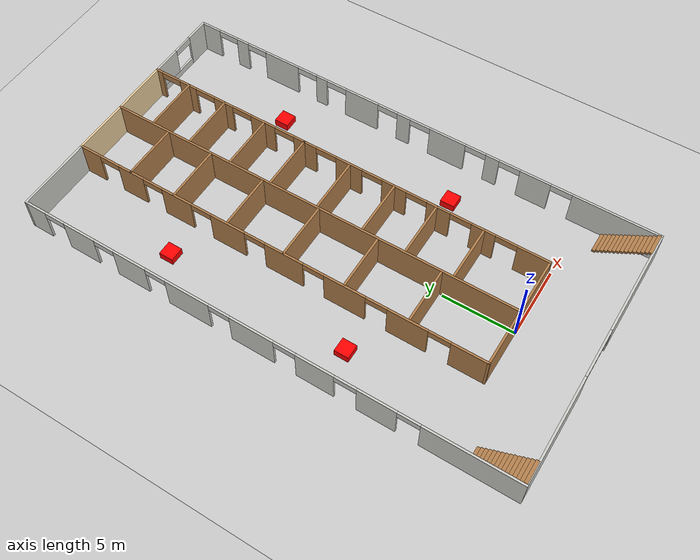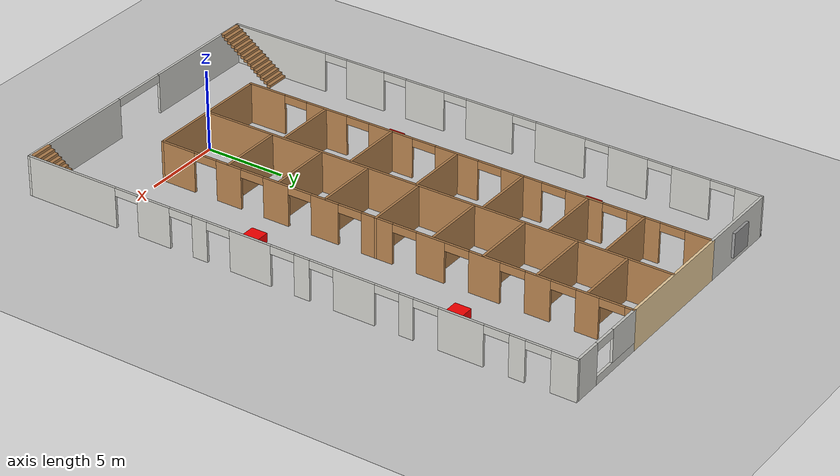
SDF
<sdf version="1.7">
 <world name="default">
  <light name="sun" type="directional">
   <pose>0 0 10 0 -0 0</pose>
   <diffuse>0.8 0.8 0.8 1</diffuse>
   <specular>0.2 0.2 0.2 1</specular>
   <attenuation>
    <range>1000</range>
    <constant>0.9</constant>
    <linear>0.01</linear>
    <quadratic>0.001</quadratic>
   </attenuation>
   <direction>-0.5 0.1 -0.9</direction>
   <spot><inner_angle>0</inner_angle><outer_angle>0</outer_angle><falloff>0</falloff></spot>
  </light>
  <model name="ground_plane">
   <static>1</static>
   <link name="link">
    <collision name="collision">
     <geometry><plane><normal>0 0 1</normal><size>100 100</size></plane></geometry>
     <surface>
      <contact><collide_bitmask>65535</collide_bitmask></contact>
      <friction><ode><mu>100</mu><mu2>50</mu2></ode></friction>
     </surface>
    </collision>
    <visual name="visual">
     <cast_shadows>0</cast_shadows>
     <geometry><plane><normal>0 0 1</normal><size>100 100</size></plane></geometry>
     <material>
      <script><uri>file://media/materials/scripts/gazebo.material</uri><name>Gazebo/Grey</name></script>
     </material>
    </visual>
   </link>
  </model>
  <gravity>0 0 -9.8</gravity>
  <magnetic_field>6e-06 2.3e-05 -4.2e-05</magnetic_field>
  <atmosphere type="adiabatic"/>
  <physics type="ode">
   <max_step_size>0.001</max_step_size>
   <real_time_factor>1</real_time_factor>
   <real_time_update_rate>1000</real_time_update_rate>
  </physics>
  <scene><ambient>0.4 0.4 0.4 1</ambient><background>0.7 0.7 0.7 1</background><shadows>1</shadows></scene>
  <spherical_coordinates>
   <surface_model>EARTH_WGS84</surface_model>
   <latitude_deg>0</latitude_deg>
   <longitude_deg>0</longitude_deg>
   <elevation>0</elevation>
   <heading_deg>0</heading_deg>
  </spherical_coordinates>
  <model name="Untitled">
   <pose>0.082155 12.4683 0 0 -0 0</pose>
   <link name="Stairs_0">
    <visual name="Stairs_0_Visual_0">
     <pose>-8.52379 -14.0578 0.083333 0 -0 0</pose>
     <geometry><box><size>1.5 0.233333 0.166667</size></box></geometry>
     <material>
      <script><uri>file://media/materials/scripts/gazebo.material</uri><name>Gazebo/Wood</name></script>
      <ambient>0.760784 0.662745 0.627451 1</ambient>
     </material>
     <meta><layer>0</layer></meta>
    </visual>
    <collision name="Stairs_0_Collision_0">
     <geometry><box><size>1.5 0.233333 0.166667</size></box></geometry>
     <pose>-8.52379 -14.0578 0.083333 0 -0 0</pose>
    </collision>
    <visual name="Stairs_0_Visual_1">
     <pose>-8.52379 -14.2912 0.25 0 -0 0</pose>
     <geometry><box><size>1.5 0.233333 0.166667</size></box></geometry>
     <material>
      <script><uri>file://media/materials/scripts/gazebo.material</uri><name>Gazebo/Wood</name></script>
      <ambient>0.760784 0.662745 0.627451 1</ambient>
     </material>
     <meta><layer>0</layer></meta>
    </visual>
    <collision name="Stairs_0_Collision_1">
     <geometry><box><size>1.5 0.233333 0.166667</size></box></geometry>
     <pose>-8.52379 -14.2912 0.25 0 -0 0</pose>
    </collision>
    <visual name="Stairs_0_Visual_2">
     <pose>-8.52379 -14.5245 0.416667 0 -0 0</pose>
     <geometry><box><size>1.5 0.233333 0.166667</size></box></geometry>
     <material>
      <script><uri>file://media/materials/scripts/gazebo.material</uri><name>Gazebo/Wood</name></script>
      <ambient>0.760784 0.662745 0.627451 1</ambient>
     </material>
     <meta><layer>0</layer></meta>
    </visual>
    <collision name="Stairs_0_Collision_2">
     <geometry><box><size>1.5 0.233333 0.166667</size></box></geometry>
     <pose>-8.52379 -14.5245 0.416667 0 -0 0</pose>
    </collision>
    <visual name="Stairs_0_Visual_3">
     <pose>-8.52379 -14.7578 0.583333 0 -0 0</pose>
     <geometry><box><size>1.5 0.233333 0.166667</size></box></geometry>
     <material>
      <script><uri>file://media/materials/scripts/gazebo.material</uri><name>Gazebo/Wood</name></script>
      <ambient>0.760784 0.662745 0.627451 1</ambient>
     </material>
     <meta><layer>0</layer></meta>
    </visual>
    <collision name="Stairs_0_Collision_3">
     <geometry><box><size>1.5 0.233333 0.166667</size></box></geometry>
     <pose>-8.52379 -14.7578 0.583333 0 -0 0</pose>
    </collision>
    <visual name="Stairs_0_Visual_4">
     <pose>-8.52379 -14.9912 0.75 0 -0 0</pose>
     <geometry><box><size>1.5 0.233333 0.166667</size></box></geometry>
     <material>
      <script><uri>file://media/materials/scripts/gazebo.material</uri><name>Gazebo/Wood</name></script>
      <ambient>0.760784 0.662745 0.627451 1</ambient>
     </material>
     <meta><layer>0</layer></meta>
    </visual>
    <collision name="Stairs_0_Collision_4">
     <geometry><box><size>1.5 0.233333 0.166667</size></box></geometry>
     <pose>-8.52379 -14.9912 0.75 0 -0 0</pose>
    </collision>
    <visual name="Stairs_0_Visual_5">
     <pose>-8.52379 -15.2245 0.916667 0 -0 0</pose>
     <geometry><box><size>1.5 0.233333 0.166667</size></box></geometry>
     <material>
      <script><uri>file://media/materials/scripts/gazebo.material</uri><name>Gazebo/Wood</name></script>
      <ambient>0.760784 0.662745 0.627451 1</ambient>
     </material>
     <meta><layer>0</layer></meta>
    </visual>
    <collision name="Stairs_0_Collision_5">
     <geometry><box><size>1.5 0.233333 0.166667</size></box></geometry>
     <pose>-8.52379 -15.2245 0.916667 0 -0 0</pose>
    </collision>
    <visual name="Stairs_0_Visual_6">
     <pose>-8.52379 -15.4578 1.08333 0 -0 0</pose>
     <geometry><box><size>1.5 0.233333 0.166667</size></box></geometry>
     <material>
      <script><uri>file://media/materials/scripts/gazebo.material</uri><name>Gazebo/Wood</name></script>
      <ambient>0.760784 0.662745 0.627451 1</ambient>
     </material>
     <meta><layer>0</layer></meta>
    </visual>
    <collision name="Stairs_0_Collision_6">
     <geometry><box><size>1.5 0.233333 0.166667</size></box></geometry>
     <pose>-8.52379 -15.4578 1.08333 0 -0 0</pose>
    </collision>
    <visual name="Stairs_0_Visual_7">
     <pose>-8.52379 -15.6912 1.25 0 -0 0</pose>
     <geometry><box><size>1.5 0.233333 0.166667</size></box></geometry>
     <material>
      <script><uri>file://media/materials/scripts/gazebo.material</uri><name>Gazebo/Wood</name></script>
      <ambient>0.760784 0.662745 0.627451 1</ambient>
     </material>
     <meta><layer>0</layer></meta>
    </visual>
    <collision name="Stairs_0_Collision_7">
     <geometry><box><size>1.5 0.233333 0.166667</size></box></geometry>
     <pose>-8.52379 -15.6912 1.25 0 -0 0</pose>
    </collision>
    <visual name="Stairs_0_Visual_8">
     <pose>-8.52379 -15.9245 1.41667 0 -0 0</pose>
     <geometry><box><size>1.5 0.233333 0.166667</size></box></geometry>
     <material>
      <script><uri>file://media/materials/scripts/gazebo.material</uri><name>Gazebo/Wood</name></script>
      <ambient>0.760784 0.662745 0.627451 1</ambient>
     </material>
     <meta><layer>0</layer></meta>
    </visual>
    <collision name="Stairs_0_Collision_8">
     <geometry><box><size>1.5 0.233333 0.166667</size></box></geometry>
     <pose>-8.52379 -15.9245 1.41667 0 -0 0</pose>
    </collision>
    <visual name="Stairs_0_Visual_9">
     <pose>-8.52379 -16.1578 1.58333 0 -0 0</pose>
     <geometry><box><size>1.5 0.233333 0.166667</size></box></geometry>
     <material>
      <script><uri>file://media/materials/scripts/gazebo.material</uri><name>Gazebo/Wood</name></script>
      <ambient>0.760784 0.662745 0.627451 1</ambient>
     </material>
     <meta><layer>0</layer></meta>
    </visual>
    <collision name="Stairs_0_Collision_9">
     <geometry><box><size>1.5 0.233333 0.166667</size></box></geometry>
     <pose>-8.52379 -16.1578 1.58333 0 -0 0</pose>
    </collision>
    <visual name="Stairs_0_Visual_10">
     <pose>-8.52379 -16.3912 1.75 0 -0 0</pose>
     <geometry><box><size>1.5 0.233333 0.166667</size></box></geometry>
     <material>
      <script><uri>file://media/materials/scripts/gazebo.material</uri><name>Gazebo/Wood</name></script>
      <ambient>0.760784 0.662745 0.627451 1</ambient>
     </material>
     <meta><layer>0</layer></meta>
    </visual>
    <collision name="Stairs_0_Collision_10">
     <geometry><box><size>1.5 0.233333 0.166667</size></box></geometry>
     <pose>-8.52379 -16.3912 1.75 0 -0 0</pose>
    </collision>
    <visual name="Stairs_0_Visual_11">
     <pose>-8.52379 -16.6245 1.91667 0 -0 0</pose>
     <geometry><box><size>1.5 0.233333 0.166667</size></box></geometry>
     <material>
      <script><uri>file://media/materials/scripts/gazebo.material</uri><name>Gazebo/Wood</name></script>
      <ambient>0.760784 0.662745 0.627451 1</ambient>
     </material>
     <meta><layer>0</layer></meta>
    </visual>
    <collision name="Stairs_0_Collision_11">
     <geometry><box><size>1.5 0.233333 0.166667</size></box></geometry>
     <pose>-8.52379 -16.6245 1.91667 0 -0 0</pose>
    </collision>
    <visual name="Stairs_0_Visual_12">
     <pose>-8.52379 -16.8578 2.08333 0 -0 0</pose>
     <geometry><box><size>1.5 0.233333 0.166667</size></box></geometry>
     <material>
      <script><uri>file://media/materials/scripts/gazebo.material</uri><name>Gazebo/Wood</name></script>
      <ambient>0.760784 0.662745 0.627451 1</ambient>
     </material>
     <meta><layer>0</layer></meta>
    </visual>
    <collision name="Stairs_0_Collision_12">
     <geometry><box><size>1.5 0.233333 0.166667</size></box></geometry>
     <pose>-8.52379 -16.8578 2.08333 0 -0 0</pose>
    </collision>
    <visual name="Stairs_0_Visual_13">
     <pose>-8.52379 -17.0912 2.25 0 -0 0</pose>
     <geometry><box><size>1.5 0.233333 0.166667</size></box></geometry>
     <material>
      <script><uri>file://media/materials/scripts/gazebo.material</uri><name>Gazebo/Wood</name></script>
      <ambient>0.760784 0.662745 0.627451 1</ambient>
     </material>
     <meta><layer>0</layer></meta>
    </visual>
    <collision name="Stairs_0_Collision_13">
     <geometry><box><size>1.5 0.233333 0.166667</size></box></geometry>
     <pose>-8.52379 -17.0912 2.25 0 -0 0</pose>
    </collision>
    <visual name="Stairs_0_Visual_14">
     <pose>-8.52379 -17.3245 2.41667 0 -0 0</pose>
     <geometry><box><size>1.5 0.233333 0.166667</size></box></geometry>
     <material>
      <script><uri>file://media/materials/scripts/gazebo.material</uri><name>Gazebo/Wood</name></script>
      <ambient>0.760784 0.662745 0.627451 1</ambient>
     </material>
     <meta><layer>0</layer></meta>
    </visual>
    <collision name="Stairs_0_Collision_14">
     <geometry><box><size>1.5 0.233333 0.166667</size></box></geometry>
     <pose>-8.52379 -17.3245 2.41667 0 -0 0</pose>
    </collision>
   </link>
   <link name="Stairs_1">
    <visual name="Stairs_1_Visual_0">
     <pose>8.59136 -14.0117 0.083333 0 -0 0</pose>
     <geometry><box><size>1.5 0.233333 0.166667</size></box></geometry>
     <material>
      <script><uri>file://media/materials/scripts/gazebo.material</uri><name>Gazebo/Wood</name></script>
      <ambient>0.760784 0.662745 0.627451 1</ambient>
     </material>
     <meta><layer>0</layer></meta>
    </visual>
    <collision name="Stairs_1_Collision_0">
     <geometry><box><size>1.5 0.233333 0.166667</size></box></geometry>
     <pose>8.59136 -14.0117 0.083333 0 -0 0</pose>
    </collision>
    <visual name="Stairs_1_Visual_1">
     <pose>8.59136 -14.2451 0.25 0 -0 0</pose>
     <geometry><box><size>1.5 0.233333 0.166667</size></box></geometry>
     <material>
      <script><uri>file://media/materials/scripts/gazebo.material</uri><name>Gazebo/Wood</name></script>
      <ambient>0.760784 0.662745 0.627451 1</ambient>
     </material>
     <meta><layer>0</layer></meta>
    </visual>
    <collision name="Stairs_1_Collision_1">
     <geometry><box><size>1.5 0.233333 0.166667</size></box></geometry>
     <pose>8.59136 -14.2451 0.25 0 -0 0</pose>
    </collision>
    <visual name="Stairs_1_Visual_2">
     <pose>8.59136 -14.4784 0.416667 0 -0 0</pose>
     <geometry><box><size>1.5 0.233333 0.166667</size></box></geometry>
     <material>
      <script><uri>file://media/materials/scripts/gazebo.material</uri><name>Gazebo/Wood</name></script>
      <ambient>0.760784 0.662745 0.627451 1</ambient>
     </material>
     <meta><layer>0</layer></meta>
    </visual>
    <collision name="Stairs_1_Collision_2">
     <geometry><box><size>1.5 0.233333 0.166667</size></box></geometry>
     <pose>8.59136 -14.4784 0.416667 0 -0 0</pose>
    </collision>
    <visual name="Stairs_1_Visual_3">
     <pose>8.59136 -14.7117 0.583333 0 -0 0</pose>
     <geometry><box><size>1.5 0.233333 0.166667</size></box></geometry>
     <material>
      <script><uri>file://media/materials/scripts/gazebo.material</uri><name>Gazebo/Wood</name></script>
      <ambient>0.760784 0.662745 0.627451 1</ambient>
     </material>
     <meta><layer>0</layer></meta>
    </visual>
    <collision name="Stairs_1_Collision_3">
     <geometry><box><size>1.5 0.233333 0.166667</size></box></geometry>
     <pose>8.59136 -14.7117 0.583333 0 -0 0</pose>
    </collision>
    <visual name="Stairs_1_Visual_4">
     <pose>8.59136 -14.9451 0.75 0 -0 0</pose>
     <geometry><box><size>1.5 0.233333 0.166667</size></box></geometry>
     <material>
      <script><uri>file://media/materials/scripts/gazebo.material</uri><name>Gazebo/Wood</name></script>
      <ambient>0.760784 0.662745 0.627451 1</ambient>
     </material>
     <meta><layer>0</layer></meta>
    </visual>
    <collision name="Stairs_1_Collision_4">
     <geometry><box><size>1.5 0.233333 0.166667</size></box></geometry>
     <pose>8.59136 -14.9451 0.75 0 -0 0</pose>
    </collision>
    <visual name="Stairs_1_Visual_5">
     <pose>8.59136 -15.1784 0.916667 0 -0 0</pose>
     <geometry><box><size>1.5 0.233333 0.166667</size></box></geometry>
     <material>
      <script><uri>file://media/materials/scripts/gazebo.material</uri><name>Gazebo/Wood</name></script>
      <ambient>0.760784 0.662745 0.627451 1</ambient>
     </material>
     <meta><layer>0</layer></meta>
    </visual>
    <collision name="Stairs_1_Collision_5">
     <geometry><box><size>1.5 0.233333 0.166667</size></box></geometry>
     <pose>8.59136 -15.1784 0.916667 0 -0 0</pose>
    </collision>
    <visual name="Stairs_1_Visual_6">
     <pose>8.59136 -15.4117 1.08333 0 -0 0</pose>
     <geometry><box><size>1.5 0.233333 0.166667</size></box></geometry>
     <material>
      <script><uri>file://media/materials/scripts/gazebo.material</uri><name>Gazebo/Wood</name></script>
      <ambient>0.760784 0.662745 0.627451 1</ambient>
     </material>
     <meta><layer>0</layer></meta>
    </visual>
    <collision name="Stairs_1_Collision_6">
     <geometry><box><size>1.5 0.233333 0.166667</size></box></geometry>
     <pose>8.59136 -15.4117 1.08333 0 -0 0</pose>
    </collision>
    <visual name="Stairs_1_Visual_7">
     <pose>8.59136 -15.6451 1.25 0 -0 0</pose>
     <geometry><box><size>1.5 0.233333 0.166667</size></box></geometry>
     <material>
      <script><uri>file://media/materials/scripts/gazebo.material</uri><name>Gazebo/Wood</name></script>
      <ambient>0.760784 0.662745 0.627451 1</ambient>
     </material>
     <meta><layer>0</layer></meta>
    </visual>
    <collision name="Stairs_1_Collision_7">
     <geometry><box><size>1.5 0.233333 0.166667</size></box></geometry>
     <pose>8.59136 -15.6451 1.25 0 -0 0</pose>
    </collision>
    <visual name="Stairs_1_Visual_8">
     <pose>8.59136 -15.8784 1.41667 0 -0 0</pose>
     <geometry><box><size>1.5 0.233333 0.166667</size></box></geometry>
     <material>
      <script><uri>file://media/materials/scripts/gazebo.material</uri><name>Gazebo/Wood</name></script>
      <ambient>0.760784 0.662745 0.627451 1</ambient>
     </material>
     <meta><layer>0</layer></meta>
    </visual>
    <collision name="Stairs_1_Collision_8">
     <geometry><box><size>1.5 0.233333 0.166667</size></box></geometry>
     <pose>8.59136 -15.8784 1.41667 0 -0 0</pose>
    </collision>
    <visual name="Stairs_1_Visual_9">
     <pose>8.59136 -16.1117 1.58333 0 -0 0</pose>
     <geometry><box><size>1.5 0.233333 0.166667</size></box></geometry>
     <material>
      <script><uri>file://media/materials/scripts/gazebo.material</uri><name>Gazebo/Wood</name></script>
      <ambient>0.760784 0.662745 0.627451 1</ambient>
     </material>
     <meta><layer>0</layer></meta>
    </visual>
    <collision name="Stairs_1_Collision_9">
     <geometry><box><size>1.5 0.233333 0.166667</size></box></geometry>
     <pose>8.59136 -16.1117 1.58333 0 -0 0</pose>
    </collision>
    <visual name="Stairs_1_Visual_10">
     <pose>8.59136 -16.3451 1.75 0 -0 0</pose>
     <geometry><box><size>1.5 0.233333 0.166667</size></box></geometry>
     <material>
      <script><uri>file://media/materials/scripts/gazebo.material</uri><name>Gazebo/Wood</name></script>
      <ambient>0.760784 0.662745 0.627451 1</ambient>
     </material>
     <meta><layer>0</layer></meta>
    </visual>
    <collision name="Stairs_1_Collision_10">
     <geometry><box><size>1.5 0.233333 0.166667</size></box></geometry>
     <pose>8.59136 -16.3451 1.75 0 -0 0</pose>
    </collision>
    <visual name="Stairs_1_Visual_11">
     <pose>8.59136 -16.5784 1.91667 0 -0 0</pose>
     <geometry><box><size>1.5 0.233333 0.166667</size></box></geometry>
     <material>
      <script><uri>file://media/materials/scripts/gazebo.material</uri><name>Gazebo/Wood</name></script>
      <ambient>0.760784 0.662745 0.627451 1</ambient>
     </material>
     <meta><layer>0</layer></meta>
    </visual>
    <collision name="Stairs_1_Collision_11">
     <geometry><box><size>1.5 0.233333 0.166667</size></box></geometry>
     <pose>8.59136 -16.5784 1.91667 0 -0 0</pose>
    </collision>
    <visual name="Stairs_1_Visual_12">
     <pose>8.59136 -16.8117 2.08333 0 -0 0</pose>
     <geometry><box><size>1.5 0.233333 0.166667</size></box></geometry>
     <material>
      <script><uri>file://media/materials/scripts/gazebo.material</uri><name>Gazebo/Wood</name></script>
      <ambient>0.760784 0.662745 0.627451 1</ambient>
     </material>
     <meta><layer>0</layer></meta>
    </visual>
    <collision name="Stairs_1_Collision_12">
     <geometry><box><size>1.5 0.233333 0.166667</size></box></geometry>
     <pose>8.59136 -16.8117 2.08333 0 -0 0</pose>
    </collision>
    <visual name="Stairs_1_Visual_13">
     <pose>8.59136 -17.0451 2.25 0 -0 0</pose>
     <geometry><box><size>1.5 0.233333 0.166667</size></box></geometry>
     <material>
      <script><uri>file://media/materials/scripts/gazebo.material</uri><name>Gazebo/Wood</name></script>
      <ambient>0.760784 0.662745 0.627451 1</ambient>
     </material>
     <meta><layer>0</layer></meta>
    </visual>
    <collision name="Stairs_1_Collision_13">
     <geometry><box><size>1.5 0.233333 0.166667</size></box></geometry>
     <pose>8.59136 -17.0451 2.25 0 -0 0</pose>
    </collision>
    <visual name="Stairs_1_Visual_14">
     <pose>8.59136 -17.2784 2.41667 0 -0 0</pose>
     <geometry><box><size>1.5 0.233333 0.166667</size></box></geometry>
     <material>
      <script><uri>file://media/materials/scripts/gazebo.material</uri><name>Gazebo/Wood</name></script>
      <ambient>0.760784 0.662745 0.627451 1</ambient>
     </material>
     <meta><layer>0</layer></meta>
    </visual>
    <collision name="Stairs_1_Collision_14">
     <geometry><box><size>1.5 0.233333 0.166667</size></box></geometry>
     <pose>8.59136 -17.2784 2.41667 0 -0 0</pose>
    </collision>
   </link>
   <link name="Wall_20">
    <pose>-4.00683 2.5 0 0 -0 1.5708</pose>
    <visual name="Wall_20_Visual_0">
     <pose>-13.7495 0 1.25 0 -0 0</pose>
     <geometry><box><size>2.50101 0.15 2.5</size></box></geometry>
     <material>
      <script><uri>file://media/materials/scripts/gazebo.material</uri><name>Gazebo/Wood</name></script>
      <ambient>1 1 1 1</ambient>
     </material>
     <meta><layer>0</layer></meta>
    </visual>
    <collision name="Wall_20_Collision_0">
     <geometry><box><size>2.50101 0.15 2.5</size></box></geometry>
     <pose>-13.7495 0 1.25 0 -0 0</pose>
    </collision>
    <visual name="Wall_20_Visual_1">
     <pose>-9.62226 0 1.25 0 -0 0</pose>
     <geometry><box><size>2.75345 0.15 2.5</size></box></geometry>
     <material>
      <script><uri>file://media/materials/scripts/gazebo.material</uri><name>Gazebo/Wood</name></script>
      <ambient>1 1 1 1</ambient>
     </material>
     <meta><layer>0</layer></meta>
    </visual>
    <collision name="Wall_20_Collision_1">
     <geometry><box><size>2.75345 0.15 2.5</size></box></geometry>
     <pose>-9.62226 0 1.25 0 -0 0</pose>
    </collision>
    <visual name="Wall_20_Visual_2">
     <pose>-5.28856 0 1.25 0 -0 0</pose>
     <geometry><box><size>2.91396 0.15 2.5</size></box></geometry>
     <material>
      <script><uri>file://media/materials/scripts/gazebo.material</uri><name>Gazebo/Wood</name></script>
      <ambient>1 1 1 1</ambient>
     </material>
     <meta><layer>0</layer></meta>
    </visual>
    <collision name="Wall_20_Collision_2">
     <geometry><box><size>2.91396 0.15 2.5</size></box></geometry>
     <pose>-5.28856 0 1.25 0 -0 0</pose>
    </collision>
    <visual name="Wall_20_Visual_3">
     <pose>-0.934819 0 1.25 0 -0 0</pose>
     <geometry><box><size>2.79352 0.15 2.5</size></box></geometry>
     <material>
      <script><uri>file://media/materials/scripts/gazebo.material</uri><name>Gazebo/Wood</name></script>
      <ambient>1 1 1 1</ambient>
     </material>
     <meta><layer>0</layer></meta>
    </visual>
    <collision name="Wall_20_Collision_3">
     <geometry><box><size>2.79352 0.15 2.5</size></box></geometry>
     <pose>-0.934819 0 1.25 0 -0 0</pose>
    </collision>
    <visual name="Wall_20_Visual_4">
     <pose>3.24723 0 1.25 0 -0 0</pose>
     <geometry><box><size>2.57057 0.15 2.5</size></box></geometry>
     <material>
      <script><uri>file://media/materials/scripts/gazebo.material</uri><name>Gazebo/Wood</name></script>
      <ambient>1 1 1 1</ambient>
     </material>
     <meta><layer>0</layer></meta>
    </visual>
    <collision name="Wall_20_Collision_4">
     <geometry><box><size>2.57057 0.15 2.5</size></box></geometry>
     <pose>3.24723 0 1.25 0 -0 0</pose>
    </collision>
    <visual name="Wall_20_Visual_5">
     <pose>7.17743 0 1.25 0 -0 0</pose>
     <geometry><box><size>2.28984 0.15 2.5</size></box></geometry>
     <material>
      <script><uri>file://media/materials/scripts/gazebo.material</uri><name>Gazebo/Wood</name></script>
      <ambient>1 1 1 1</ambient>
     </material>
     <meta><layer>0</layer></meta>
    </visual>
    <collision name="Wall_20_Collision_5">
     <geometry><box><size>2.28984 0.15 2.5</size></box></geometry>
     <pose>7.17743 0 1.25 0 -0 0</pose>
    </collision>
    <visual name="Wall_20_Visual_6">
     <pose>10.8237 0 1.25 0 -0 0</pose>
     <geometry><box><size>2.00266 0.15 2.5</size></box></geometry>
     <material>
      <script><uri>file://media/materials/scripts/gazebo.material</uri><name>Gazebo/Wood</name></script>
      <ambient>1 1 1 1</ambient>
     </material>
     <meta><layer>0</layer></meta>
    </visual>
    <collision name="Wall_20_Collision_6">
     <geometry><box><size>2.00266 0.15 2.5</size></box></geometry>
     <pose>10.8237 0 1.25 0 -0 0</pose>
    </collision>
    <visual name="Wall_20_Visual_7">
     <pose>14.1625 0 1.25 0 -0 0</pose>
     <geometry><box><size>1.675 0.15 2.5</size></box></geometry>
     <material>
      <script><uri>file://media/materials/scripts/gazebo.material</uri><name>Gazebo/Wood</name></script>
      <ambient>1 1 1 1</ambient>
     </material>
     <meta><layer>0</layer></meta>
    </visual>
    <collision name="Wall_20_Collision_7">
     <geometry><box><size>1.675 0.15 2.5</size></box></geometry>
     <pose>14.1625 0 1.25 0 -0 0</pose>
    </collision>
    <visual name="Wall_20_Visual_8">
     <pose>-11.749 0 2.25 0 -0 0</pose>
     <geometry><box><size>1.5 0.15 0.5</size></box></geometry>
     <material>
      <script><uri>file://media/materials/scripts/gazebo.material</uri><name>Gazebo/Wood</name></script>
      <ambient>1 1 1 1</ambient>
     </material>
     <meta><layer>0</layer></meta>
    </visual>
    <collision name="Wall_20_Collision_8">
     <geometry><box><size>1.5 0.15 0.5</size></box></geometry>
     <pose>-11.749 0 2.25 0 -0 0</pose>
    </collision>
    <visual name="Wall_20_Visual_9">
     <pose>-7.49554 0 2.25 0 -0 0</pose>
     <geometry><box><size>1.5 0.15 0.5</size></box></geometry>
     <material>
      <script><uri>file://media/materials/scripts/gazebo.material</uri><name>Gazebo/Wood</name></script>
      <ambient>1 1 1 1</ambient>
     </material>
     <meta><layer>0</layer></meta>
    </visual>
    <collision name="Wall_20_Collision_9">
     <geometry><box><size>1.5 0.15 0.5</size></box></geometry>
     <pose>-7.49554 0 2.25 0 -0 0</pose>
    </collision>
    <visual name="Wall_20_Visual_10">
     <pose>-3.08158 0 2.25 0 -0 0</pose>
     <geometry><box><size>1.5 0.15 0.5</size></box></geometry>
     <material>
      <script><uri>file://media/materials/scripts/gazebo.material</uri><name>Gazebo/Wood</name></script>
      <ambient>1 1 1 1</ambient>
     </material>
     <meta><layer>0</layer></meta>
    </visual>
    <collision name="Wall_20_Collision_10">
     <geometry><box><size>1.5 0.15 0.5</size></box></geometry>
     <pose>-3.08158 0 2.25 0 -0 0</pose>
    </collision>
    <visual name="Wall_20_Visual_11">
     <pose>1.21194 0 2.25 0 -0 0</pose>
     <geometry><box><size>1.5 0.15 0.5</size></box></geometry>
     <material>
      <script><uri>file://media/materials/scripts/gazebo.material</uri><name>Gazebo/Wood</name></script>
      <ambient>1 1 1 1</ambient>
     </material>
     <meta><layer>0</layer></meta>
    </visual>
    <collision name="Wall_20_Collision_11">
     <geometry><box><size>1.5 0.15 0.5</size></box></geometry>
     <pose>1.21194 0 2.25 0 -0 0</pose>
    </collision>
    <visual name="Wall_20_Visual_12">
     <pose>5.28251 0 2.25 0 -0 0</pose>
     <geometry><box><size>1.5 0.15 0.5</size></box></geometry>
     <material>
      <script><uri>file://media/materials/scripts/gazebo.material</uri><name>Gazebo/Wood</name></script>
      <ambient>1 1 1 1</ambient>
     </material>
     <meta><layer>0</layer></meta>
    </visual>
    <collision name="Wall_20_Collision_12">
     <geometry><box><size>1.5 0.15 0.5</size></box></geometry>
     <pose>5.28251 0 2.25 0 -0 0</pose>
    </collision>
    <visual name="Wall_20_Visual_13">
     <pose>9.07234 0 2.25 0 -0 0</pose>
     <geometry><box><size>1.5 0.15 0.5</size></box></geometry>
     <material>
      <script><uri>file://media/materials/scripts/gazebo.material</uri><name>Gazebo/Wood</name></script>
      <ambient>1 1 1 1</ambient>
     </material>
     <meta><layer>0</layer></meta>
    </visual>
    <collision name="Wall_20_Collision_13">
     <geometry><box><size>1.5 0.15 0.5</size></box></geometry>
     <pose>9.07234 0 2.25 0 -0 0</pose>
    </collision>
    <visual name="Wall_20_Visual_14">
     <pose>12.575 0 2.25 0 -0 0</pose>
     <geometry><box><size>1.5 0.15 0.5</size></box></geometry>
     <material>
      <script><uri>file://media/materials/scripts/gazebo.material</uri><name>Gazebo/Wood</name></script>
      <ambient>1 1 1 1</ambient>
     </material>
     <meta><layer>0</layer></meta>
    </visual>
    <collision name="Wall_20_Collision_14">
     <geometry><box><size>1.5 0.15 0.5</size></box></geometry>
     <pose>12.575 0 2.25 0 -0 0</pose>
    </collision>
   </link>
   <link name="Wall_23">
    <collision name="Wall_23_Collision">
     <geometry><box><size>5.5 0.15 2.5</size></box></geometry>
     <pose>0 0 1.25 0 -0 0</pose>
    </collision>
    <visual name="Wall_23_Visual">
     <pose>0 0 1.25 0 -0 0</pose>
     <geometry><box><size>5.5 0.15 2.5</size></box></geometry>
     <material>
      <script><uri>file://media/materials/scripts/gazebo.material</uri><name>Gazebo/CeilingTiled</name></script>
      <ambient>0.921569 0.807843 0.615686 1</ambient>
     </material>
     <meta><layer>0</layer></meta>
    </visual>
    <pose>-6.68183 17.425 0 0 -0 3.14159</pose>
   </link>
   <link name="Wall_28">
    <pose>9.35683 0 0 0 -0 -1.5708</pose>
    <visual name="Wall_28_Visual_0">
     <pose>-16.7222 0 1.25 0 -0 0</pose>
     <geometry><box><size>1.5557 0.15 2.5</size></box></geometry>
     <material>
      <script><uri>file://media/materials/scripts/gazebo.material</uri><name>Gazebo/CeilingTiled</name></script>
      <ambient>0.921569 0.807843 0.615686 1</ambient>
     </material>
     <meta><layer>0</layer></meta>
    </visual>
    <collision name="Wall_28_Collision_0">
     <geometry><box><size>1.5557 0.15 2.5</size></box></geometry>
     <pose>-16.7222 0 1.25 0 -0 0</pose>
    </collision>
    <visual name="Wall_28_Visual_1">
     <pose>-13.9727 0 1.25 0 -0 0</pose>
     <geometry><box><size>0.943169 0.15 2.5</size></box></geometry>
     <material>
      <script><uri>file://media/materials/scripts/gazebo.material</uri><name>Gazebo/CeilingTiled</name></script>
      <ambient>0.921569 0.807843 0.615686 1</ambient>
     </material>
     <meta><layer>0</layer></meta>
    </visual>
    <collision name="Wall_28_Collision_1">
     <geometry><box><size>0.943169 0.15 2.5</size></box></geometry>
     <pose>-13.9727 0 1.25 0 -0 0</pose>
    </collision>
    <visual name="Wall_28_Visual_2">
     <pose>-10.6457 0 1.25 0 -0 0</pose>
     <geometry><box><size>2.71078 0.15 2.5</size></box></geometry>
     <material>
      <script><uri>file://media/materials/scripts/gazebo.material</uri><name>Gazebo/CeilingTiled</name></script>
      <ambient>0.921569 0.807843 0.615686 1</ambient>
     </material>
     <meta><layer>0</layer></meta>
    </visual>
    <collision name="Wall_28_Collision_2">
     <geometry><box><size>2.71078 0.15 2.5</size></box></geometry>
     <pose>-10.6457 0 1.25 0 -0 0</pose>
    </collision>
    <visual name="Wall_28_Visual_3">
     <pose>-7.35399 0 1.25 0 -0 0</pose>
     <geometry><box><size>0.872719 0.15 2.5</size></box></geometry>
     <material>
      <script><uri>file://media/materials/scripts/gazebo.material</uri><name>Gazebo/CeilingTiled</name></script>
      <ambient>0.921569 0.807843 0.615686 1</ambient>
     </material>
     <meta><layer>0</layer></meta>
    </visual>
    <collision name="Wall_28_Collision_3">
     <geometry><box><size>0.872719 0.15 2.5</size></box></geometry>
     <pose>-7.35399 0 1.25 0 -0 0</pose>
    </collision>
    <visual name="Wall_28_Visual_4">
     <pose>-4.13625 0 1.25 0 -0 0</pose>
     <geometry><box><size>2.56276 0.15 2.5</size></box></geometry>
     <material>
      <script><uri>file://media/materials/scripts/gazebo.material</uri><name>Gazebo/CeilingTiled</name></script>
      <ambient>0.921569 0.807843 0.615686 1</ambient>
     </material>
     <meta><layer>0</layer></meta>
    </visual>
    <collision name="Wall_28_Collision_4">
     <geometry><box><size>2.56276 0.15 2.5</size></box></geometry>
     <pose>-4.13625 0 1.25 0 -0 0</pose>
    </collision>
    <visual name="Wall_28_Visual_5">
     <pose>-0.865969 0 1.25 0 -0 0</pose>
     <geometry><box><size>0.977809 0.15 2.5</size></box></geometry>
     <material>
      <script><uri>file://media/materials/scripts/gazebo.material</uri><name>Gazebo/CeilingTiled</name></script>
      <ambient>0.921569 0.807843 0.615686 1</ambient>
     </material>
     <meta><layer>0</layer></meta>
    </visual>
    <collision name="Wall_28_Collision_5">
     <geometry><box><size>0.977809 0.15 2.5</size></box></geometry>
     <pose>-0.865969 0 1.25 0 -0 0</pose>
    </collision>
    <visual name="Wall_28_Visual_6">
     <pose>2.45268 0 1.25 0 -0 0</pose>
     <geometry><box><size>2.6595 0.15 2.5</size></box></geometry>
     <material>
      <script><uri>file://media/materials/scripts/gazebo.material</uri><name>Gazebo/CeilingTiled</name></script>
      <ambient>0.921569 0.807843 0.615686 1</ambient>
     </material>
     <meta><layer>0</layer></meta>
    </visual>
    <collision name="Wall_28_Collision_6">
     <geometry><box><size>2.6595 0.15 2.5</size></box></geometry>
     <pose>2.45268 0 1.25 0 -0 0</pose>
    </collision>
    <visual name="Wall_28_Visual_7">
     <pose>5.76934 0 1.25 0 -0 0</pose>
     <geometry><box><size>0.973819 0.15 2.5</size></box></geometry>
     <material>
      <script><uri>file://media/materials/scripts/gazebo.material</uri><name>Gazebo/CeilingTiled</name></script>
      <ambient>0.921569 0.807843 0.615686 1</ambient>
     </material>
     <meta><layer>0</layer></meta>
    </visual>
    <collision name="Wall_28_Collision_7">
     <geometry><box><size>0.973819 0.15 2.5</size></box></geometry>
     <pose>5.76934 0 1.25 0 -0 0</pose>
    </collision>
    <visual name="Wall_28_Visual_8">
     <pose>8.84167 0 1.25 0 -0 0</pose>
     <geometry><box><size>2.17083 0.15 2.5</size></box></geometry>
     <material>
      <script><uri>file://media/materials/scripts/gazebo.material</uri><name>Gazebo/CeilingTiled</name></script>
      <ambient>0.921569 0.807843 0.615686 1</ambient>
     </material>
     <meta><layer>0</layer></meta>
    </visual>
    <collision name="Wall_28_Collision_8">
     <geometry><box><size>2.17083 0.15 2.5</size></box></geometry>
     <pose>8.84167 0 1.25 0 -0 0</pose>
    </collision>
    <visual name="Wall_28_Visual_9">
     <pose>14.4635 0 1.25 0 -0 0</pose>
     <geometry><box><size>6.07292 0.15 2.5</size></box></geometry>
     <material>
      <script><uri>file://media/materials/scripts/gazebo.material</uri><name>Gazebo/CeilingTiled</name></script>
      <ambient>0.921569 0.807843 0.615686 1</ambient>
     </material>
     <meta><layer>0</layer></meta>
    </visual>
    <collision name="Wall_28_Collision_9">
     <geometry><box><size>6.07292 0.15 2.5</size></box></geometry>
     <pose>14.4635 0 1.25 0 -0 0</pose>
    </collision>
    <visual name="Wall_28_Visual_10">
     <pose>-15.1943 0 2.25 0 -0 0</pose>
     <geometry><box><size>1.5 0.15 0.5</size></box></geometry>
     <material>
      <script><uri>file://media/materials/scripts/gazebo.material</uri><name>Gazebo/CeilingTiled</name></script>
      <ambient>0.921569 0.807843 0.615686 1</ambient>
     </material>
     <meta><layer>0</layer></meta>
    </visual>
    <collision name="Wall_28_Collision_10">
     <geometry><box><size>1.5 0.15 0.5</size></box></geometry>
     <pose>-15.1943 0 2.25 0 -0 0</pose>
    </collision>
    <visual name="Wall_28_Visual_11">
     <pose>-12.7511 0 2.25 0 -0 0</pose>
     <geometry><box><size>1.5 0.15 0.5</size></box></geometry>
     <material>
      <script><uri>file://media/materials/scripts/gazebo.material</uri><name>Gazebo/CeilingTiled</name></script>
      <ambient>0.921569 0.807843 0.615686 1</ambient>
     </material>
     <meta><layer>0</layer></meta>
    </visual>
    <collision name="Wall_28_Collision_11">
     <geometry><box><size>1.5 0.15 0.5</size></box></geometry>
     <pose>-12.7511 0 2.25 0 -0 0</pose>
    </collision>
    <visual name="Wall_28_Visual_12">
     <pose>-8.54035 0 2.25 0 -0 0</pose>
     <geometry><box><size>1.5 0.15 0.5</size></box></geometry>
     <material>
      <script><uri>file://media/materials/scripts/gazebo.material</uri><name>Gazebo/CeilingTiled</name></script>
      <ambient>0.921569 0.807843 0.615686 1</ambient>
     </material>
     <meta><layer>0</layer></meta>
    </visual>
    <collision name="Wall_28_Collision_12">
     <geometry><box><size>1.5 0.15 0.5</size></box></geometry>
     <pose>-8.54035 0 2.25 0 -0 0</pose>
    </collision>
    <visual name="Wall_28_Visual_13">
     <pose>-6.16763 0 2.25 0 -0 0</pose>
     <geometry><box><size>1.5 0.15 0.5</size></box></geometry>
     <material>
      <script><uri>file://media/materials/scripts/gazebo.material</uri><name>Gazebo/CeilingTiled</name></script>
      <ambient>0.921569 0.807843 0.615686 1</ambient>
     </material>
     <meta><layer>0</layer></meta>
    </visual>
    <collision name="Wall_28_Collision_13">
     <geometry><box><size>1.5 0.15 0.5</size></box></geometry>
     <pose>-6.16763 0 2.25 0 -0 0</pose>
    </collision>
    <visual name="Wall_28_Visual_14">
     <pose>-2.10487 0 2.25 0 -0 0</pose>
     <geometry><box><size>1.5 0.15 0.5</size></box></geometry>
     <material>
      <script><uri>file://media/materials/scripts/gazebo.material</uri><name>Gazebo/CeilingTiled</name></script>
      <ambient>0.921569 0.807843 0.615686 1</ambient>
     </material>
     <meta><layer>0</layer></meta>
    </visual>
    <collision name="Wall_28_Collision_14">
     <geometry><box><size>1.5 0.15 0.5</size></box></geometry>
     <pose>-2.10487 0 2.25 0 -0 0</pose>
    </collision>
    <visual name="Wall_28_Visual_15">
     <pose>0.372935 0 2.25 0 -0 0</pose>
     <geometry><box><size>1.5 0.15 0.5</size></box></geometry>
     <material>
      <script><uri>file://media/materials/scripts/gazebo.material</uri><name>Gazebo/CeilingTiled</name></script>
      <ambient>0.921569 0.807843 0.615686 1</ambient>
     </material>
     <meta><layer>0</layer></meta>
    </visual>
    <collision name="Wall_28_Collision_15">
     <geometry><box><size>1.5 0.15 0.5</size></box></geometry>
     <pose>0.372935 0 2.25 0 -0 0</pose>
    </collision>
    <visual name="Wall_28_Visual_16">
     <pose>4.53243 0 2.25 0 -0 0</pose>
     <geometry><box><size>1.5 0.15 0.5</size></box></geometry>
     <material>
      <script><uri>file://media/materials/scripts/gazebo.material</uri><name>Gazebo/CeilingTiled</name></script>
      <ambient>0.921569 0.807843 0.615686 1</ambient>
     </material>
     <meta><layer>0</layer></meta>
    </visual>
    <collision name="Wall_28_Collision_16">
     <geometry><box><size>1.5 0.15 0.5</size></box></geometry>
     <pose>4.53243 0 2.25 0 -0 0</pose>
    </collision>
    <visual name="Wall_28_Visual_17">
     <pose>7.00625 0 2.25 0 -0 0</pose>
     <geometry><box><size>1.5 0.15 0.5</size></box></geometry>
     <material>
      <script><uri>file://media/materials/scripts/gazebo.material</uri><name>Gazebo/CeilingTiled</name></script>
      <ambient>0.921569 0.807843 0.615686 1</ambient>
     </material>
     <meta><layer>0</layer></meta>
    </visual>
    <collision name="Wall_28_Collision_17">
     <geometry><box><size>1.5 0.15 0.5</size></box></geometry>
     <pose>7.00625 0 2.25 0 -0 0</pose>
    </collision>
    <visual name="Wall_28_Visual_18">
     <pose>10.6771 0 2.25 0 -0 0</pose>
     <geometry><box><size>1.5 0.15 0.5</size></box></geometry>
     <material>
      <script><uri>file://media/materials/scripts/gazebo.material</uri><name>Gazebo/CeilingTiled</name></script>
      <ambient>0.921569 0.807843 0.615686 1</ambient>
     </material>
     <meta><layer>0</layer></meta>
    </visual>
    <collision name="Wall_28_Collision_18">
     <geometry><box><size>1.5 0.15 0.5</size></box></geometry>
     <pose>10.6771 0 2.25 0 -0 0</pose>
    </collision>
   </link>
   <link name="Wall_32">
    <pose>-9.35683 0 0 0 -0 -1.5708</pose>
    <visual name="Wall_32_Visual_0">
     <pose>-16.6643 0 1.25 0 -0 0</pose>
     <geometry><box><size>1.67142 0.15 2.5</size></box></geometry>
     <material>
      <script><uri>file://media/materials/scripts/gazebo.material</uri><name>Gazebo/CeilingTiled</name></script>
      <ambient>0.921569 0.807843 0.615686 1</ambient>
     </material>
     <meta><layer>0</layer></meta>
    </visual>
    <collision name="Wall_32_Collision_0">
     <geometry><box><size>1.67142 0.15 2.5</size></box></geometry>
     <pose>-16.6643 0 1.25 0 -0 0</pose>
    </collision>
    <visual name="Wall_32_Visual_1">
     <pose>-13.1416 0 1.25 0 -0 0</pose>
     <geometry><box><size>2.37406 0.15 2.5</size></box></geometry>
     <material>
      <script><uri>file://media/materials/scripts/gazebo.material</uri><name>Gazebo/CeilingTiled</name></script>
      <ambient>0.921569 0.807843 0.615686 1</ambient>
     </material>
     <meta><layer>0</layer></meta>
    </visual>
    <collision name="Wall_32_Collision_1">
     <geometry><box><size>2.37406 0.15 2.5</size></box></geometry>
     <pose>-13.1416 0 1.25 0 -0 0</pose>
    </collision>
    <visual name="Wall_32_Visual_2">
     <pose>-9.22261 0 1.25 0 -0 0</pose>
     <geometry><box><size>2.46382 0.15 2.5</size></box></geometry>
     <material>
      <script><uri>file://media/materials/scripts/gazebo.material</uri><name>Gazebo/CeilingTiled</name></script>
      <ambient>0.921569 0.807843 0.615686 1</ambient>
     </material>
     <meta><layer>0</layer></meta>
    </visual>
    <collision name="Wall_32_Collision_2">
     <geometry><box><size>2.46382 0.15 2.5</size></box></geometry>
     <pose>-9.22261 0 1.25 0 -0 0</pose>
    </collision>
    <visual name="Wall_32_Visual_3">
     <pose>-4.89246 0 1.25 0 -0 0</pose>
     <geometry><box><size>3.19648 0.15 2.5</size></box></geometry>
     <material>
      <script><uri>file://media/materials/scripts/gazebo.material</uri><name>Gazebo/CeilingTiled</name></script>
      <ambient>0.921569 0.807843 0.615686 1</ambient>
     </material>
     <meta><layer>0</layer></meta>
    </visual>
    <collision name="Wall_32_Collision_3">
     <geometry><box><size>3.19648 0.15 2.5</size></box></geometry>
     <pose>-4.89246 0 1.25 0 -0 0</pose>
    </collision>
    <visual name="Wall_32_Visual_4">
     <pose>-0.243282 0 1.25 0 -0 0</pose>
     <geometry><box><size>3.10188 0.15 2.5</size></box></geometry>
     <material>
      <script><uri>file://media/materials/scripts/gazebo.material</uri><name>Gazebo/CeilingTiled</name></script>
      <ambient>0.921569 0.807843 0.615686 1</ambient>
     </material>
     <meta><layer>0</layer></meta>
    </visual>
    <collision name="Wall_32_Collision_4">
     <geometry><box><size>3.10188 0.15 2.5</size></box></geometry>
     <pose>-0.243282 0 1.25 0 -0 0</pose>
    </collision>
    <visual name="Wall_32_Visual_5">
     <pose>4.11575 0 1.25 0 -0 0</pose>
     <geometry><box><size>2.61618 0.15 2.5</size></box></geometry>
     <material>
      <script><uri>file://media/materials/scripts/gazebo.material</uri><name>Gazebo/CeilingTiled</name></script>
      <ambient>0.921569 0.807843 0.615686 1</ambient>
     </material>
     <meta><layer>0</layer></meta>
    </visual>
    <collision name="Wall_32_Collision_5">
     <geometry><box><size>2.61618 0.15 2.5</size></box></geometry>
     <pose>4.11575 0 1.25 0 -0 0</pose>
    </collision>
    <visual name="Wall_32_Visual_6">
     <pose>8.23193 0 1.25 0 -0 0</pose>
     <geometry><box><size>2.61618 0.15 2.5</size></box></geometry>
     <material>
      <script><uri>file://media/materials/scripts/gazebo.material</uri><name>Gazebo/CeilingTiled</name></script>
      <ambient>0.921569 0.807843 0.615686 1</ambient>
     </material>
     <meta><layer>0</layer></meta>
    </visual>
    <collision name="Wall_32_Collision_6">
     <geometry><box><size>2.61618 0.15 2.5</size></box></geometry>
     <pose>8.23193 0 1.25 0 -0 0</pose>
    </collision>
    <visual name="Wall_32_Visual_7">
     <pose>14.27 0 1.25 0 -0 0</pose>
     <geometry><box><size>6.45998 0.15 2.5</size></box></geometry>
     <material>
      <script><uri>file://media/materials/scripts/gazebo.material</uri><name>Gazebo/CeilingTiled</name></script>
      <ambient>0.921569 0.807843 0.615686 1</ambient>
     </material>
     <meta><layer>0</layer></meta>
    </visual>
    <collision name="Wall_32_Collision_7">
     <geometry><box><size>6.45998 0.15 2.5</size></box></geometry>
     <pose>14.27 0 1.25 0 -0 0</pose>
    </collision>
    <visual name="Wall_32_Visual_8">
     <pose>-15.0786 0 2.25 0 -0 0</pose>
     <geometry><box><size>1.5 0.15 0.5</size></box></geometry>
     <material>
      <script><uri>file://media/materials/scripts/gazebo.material</uri><name>Gazebo/CeilingTiled</name></script>
      <ambient>0.921569 0.807843 0.615686 1</ambient>
     </material>
     <meta><layer>0</layer></meta>
    </visual>
    <collision name="Wall_32_Collision_8">
     <geometry><box><size>1.5 0.15 0.5</size></box></geometry>
     <pose>-15.0786 0 2.25 0 -0 0</pose>
    </collision>
    <visual name="Wall_32_Visual_9">
     <pose>-11.2045 0 2.25 0 -0 0</pose>
     <geometry><box><size>1.5 0.15 0.5</size></box></geometry>
     <material>
      <script><uri>file://media/materials/scripts/gazebo.material</uri><name>Gazebo/CeilingTiled</name></script>
      <ambient>0.921569 0.807843 0.615686 1</ambient>
     </material>
     <meta><layer>0</layer></meta>
    </visual>
    <collision name="Wall_32_Collision_9">
     <geometry><box><size>1.5 0.15 0.5</size></box></geometry>
     <pose>-11.2045 0 2.25 0 -0 0</pose>
    </collision>
    <visual name="Wall_32_Visual_10">
     <pose>-7.2407 0 2.25 0 -0 0</pose>
     <geometry><box><size>1.5 0.15 0.5</size></box></geometry>
     <material>
      <script><uri>file://media/materials/scripts/gazebo.material</uri><name>Gazebo/CeilingTiled</name></script>
      <ambient>0.921569 0.807843 0.615686 1</ambient>
     </material>
     <meta><layer>0</layer></meta>
    </visual>
    <collision name="Wall_32_Collision_10">
     <geometry><box><size>1.5 0.15 0.5</size></box></geometry>
     <pose>-7.2407 0 2.25 0 -0 0</pose>
    </collision>
    <visual name="Wall_32_Visual_11">
     <pose>-2.54422 0 2.25 0 -0 0</pose>
     <geometry><box><size>1.5 0.15 0.5</size></box></geometry>
     <material>
      <script><uri>file://media/materials/scripts/gazebo.material</uri><name>Gazebo/CeilingTiled</name></script>
      <ambient>0.921569 0.807843 0.615686 1</ambient>
     </material>
     <meta><layer>0</layer></meta>
    </visual>
    <collision name="Wall_32_Collision_11">
     <geometry><box><size>1.5 0.15 0.5</size></box></geometry>
     <pose>-2.54422 0 2.25 0 -0 0</pose>
    </collision>
    <visual name="Wall_32_Visual_12">
     <pose>2.05766 0 2.25 0 -0 0</pose>
     <geometry><box><size>1.5 0.15 0.5</size></box></geometry>
     <material>
      <script><uri>file://media/materials/scripts/gazebo.material</uri><name>Gazebo/CeilingTiled</name></script>
      <ambient>0.921569 0.807843 0.615686 1</ambient>
     </material>
     <meta><layer>0</layer></meta>
    </visual>
    <collision name="Wall_32_Collision_12">
     <geometry><box><size>1.5 0.15 0.5</size></box></geometry>
     <pose>2.05766 0 2.25 0 -0 0</pose>
    </collision>
    <visual name="Wall_32_Visual_13">
     <pose>6.17384 0 2.25 0 -0 0</pose>
     <geometry><box><size>1.5 0.15 0.5</size></box></geometry>
     <material>
      <script><uri>file://media/materials/scripts/gazebo.material</uri><name>Gazebo/CeilingTiled</name></script>
      <ambient>0.921569 0.807843 0.615686 1</ambient>
     </material>
     <meta><layer>0</layer></meta>
    </visual>
    <collision name="Wall_32_Collision_13">
     <geometry><box><size>1.5 0.15 0.5</size></box></geometry>
     <pose>6.17384 0 2.25 0 -0 0</pose>
    </collision>
    <visual name="Wall_32_Visual_14">
     <pose>10.29 0 2.25 0 -0 0</pose>
     <geometry><box><size>1.5 0.15 0.5</size></box></geometry>
     <material>
      <script><uri>file://media/materials/scripts/gazebo.material</uri><name>Gazebo/CeilingTiled</name></script>
      <ambient>0.921569 0.807843 0.615686 1</ambient>
     </material>
     <meta><layer>0</layer></meta>
    </visual>
    <collision name="Wall_32_Collision_14">
     <geometry><box><size>1.5 0.15 0.5</size></box></geometry>
     <pose>10.29 0 2.25 0 -0 0</pose>
    </collision>
   </link>
   <link name="Wall_34">
    <pose>0 -17.425 0 0 -0 3.14159</pose>
    <visual name="Wall_34_Visual_0">
     <pose>-5.54402 0 1.25 0 -0 0</pose>
     <geometry><box><size>7.77563 0.15 2.5</size></box></geometry>
     <material>
      <script><uri>file://media/materials/scripts/gazebo.material</uri><name>Gazebo/CeilingTiled</name></script>
      <ambient>0.760784 0.662745 0.627451 1</ambient>
     </material>
     <meta><layer>0</layer></meta>
    </visual>
    <collision name="Wall_34_Collision_0">
     <geometry><box><size>7.77563 0.15 2.5</size></box></geometry>
     <pose>-5.54402 0 1.25 0 -0 0</pose>
    </collision>
    <visual name="Wall_34_Visual_1">
     <pose>5.63781 0 1.25 0 -0 0</pose>
     <geometry><box><size>7.58804 0.15 2.5</size></box></geometry>
     <material>
      <script><uri>file://media/materials/scripts/gazebo.material</uri><name>Gazebo/CeilingTiled</name></script>
      <ambient>0.760784 0.662745 0.627451 1</ambient>
     </material>
     <meta><layer>0</layer></meta>
    </visual>
    <collision name="Wall_34_Collision_1">
     <geometry><box><size>7.58804 0.15 2.5</size></box></geometry>
     <pose>5.63781 0 1.25 0 -0 0</pose>
    </collision>
    <visual name="Wall_34_Visual_2">
     <pose>0.093795 0 2.25 0 -0 0</pose>
     <geometry><box><size>3.5 0.15 0.5</size></box></geometry>
     <material>
      <script><uri>file://media/materials/scripts/gazebo.material</uri><name>Gazebo/CeilingTiled</name></script>
      <ambient>0.760784 0.662745 0.627451 1</ambient>
     </material>
     <meta><layer>0</layer></meta>
    </visual>
    <collision name="Wall_34_Collision_2">
     <geometry><box><size>3.5 0.15 0.5</size></box></geometry>
     <pose>0.093795 0 2.25 0 -0 0</pose>
    </collision>
   </link>
   <link name="Wall_40">
    <pose>6.68183 17.425 0 0 -0 3.14159</pose>
    <visual name="Wall_40_Visual_0">
     <pose>-1.83447 0 1.25 0 -0 0</pose>
     <geometry><box><size>1.83106 0.15 2.5</size></box></geometry>
     <material>
      <script><uri>file://media/materials/scripts/gazebo.material</uri><name>Gazebo/CeilingTiled</name></script>
      <ambient>0.921569 0.807843 0.615686 1</ambient>
     </material>
     <meta><layer>0</layer></meta>
    </visual>
    <collision name="Wall_40_Collision_0">
     <geometry><box><size>1.83106 0.15 2.5</size></box></geometry>
     <pose>-1.83447 0 1.25 0 -0 0</pose>
    </collision>
    <visual name="Wall_40_Visual_1">
     <pose>0.915531 0 0.25 0 -0 0</pose>
     <geometry><box><size>3.66894 0.15 0.5</size></box></geometry>
     <material>
      <script><uri>file://media/materials/scripts/gazebo.material</uri><name>Gazebo/CeilingTiled</name></script>
      <ambient>0.921569 0.807843 0.615686 1</ambient>
     </material>
     <meta><layer>0</layer></meta>
    </visual>
    <collision name="Wall_40_Collision_1">
     <geometry><box><size>3.66894 0.15 0.5</size></box></geometry>
     <pose>0.915531 0 0.25 0 -0 0</pose>
    </collision>
    <visual name="Wall_40_Visual_2">
     <pose>1.66553 0 1.5 0 -0 0</pose>
     <geometry><box><size>2.16894 0.15 2</size></box></geometry>
     <material>
      <script><uri>file://media/materials/scripts/gazebo.material</uri><name>Gazebo/CeilingTiled</name></script>
      <ambient>0.921569 0.807843 0.615686 1</ambient>
     </material>
     <meta><layer>0</layer></meta>
    </visual>
    <collision name="Wall_40_Collision_2">
     <geometry><box><size>2.16894 0.15 2</size></box></geometry>
     <pose>1.66553 0 1.5 0 -0 0</pose>
    </collision>
    <visual name="Wall_40_Visual_3">
     <pose>-0.168938 0 2.25 0 -0 0</pose>
     <geometry><box><size>1.5 0.15 0.5</size></box></geometry>
     <material>
      <script><uri>file://media/materials/scripts/gazebo.material</uri><name>Gazebo/CeilingTiled</name></script>
      <ambient>0.921569 0.807843 0.615686 1</ambient>
     </material>
     <meta><layer>0</layer></meta>
    </visual>
    <collision name="Wall_40_Collision_3">
     <geometry><box><size>1.5 0.15 0.5</size></box></geometry>
     <pose>-0.168938 0 2.25 0 -0 0</pose>
    </collision>
   </link>
   <link name="Wall_43">
    <pose>4.00683 2.5 0 0 -0 -1.5708</pose>
    <visual name="Wall_43_Visual_0">
     <pose>-14.7194 0 1.25 0 -0 0</pose>
     <geometry><box><size>0.561153 0.15 2.5</size></box></geometry>
     <material>
      <script><uri>file://media/materials/scripts/gazebo.material</uri><name>Gazebo/Wood</name></script>
      <ambient>1 1 1 1</ambient>
     </material>
     <meta><layer>0</layer></meta>
    </visual>
    <collision name="Wall_43_Collision_0">
     <geometry><box><size>0.561153 0.15 2.5</size></box></geometry>
     <pose>-14.7194 0 1.25 0 -0 0</pose>
    </collision>
    <visual name="Wall_43_Visual_1">
     <pose>-12.2543 0 1.25 0 -0 0</pose>
     <geometry><box><size>1.36904 0.15 2.5</size></box></geometry>
     <material>
      <script><uri>file://media/materials/scripts/gazebo.material</uri><name>Gazebo/Wood</name></script>
      <ambient>1 1 1 1</ambient>
     </material>
     <meta><layer>0</layer></meta>
    </visual>
    <collision name="Wall_43_Collision_1">
     <geometry><box><size>1.36904 0.15 2.5</size></box></geometry>
     <pose>-12.2543 0 1.25 0 -0 0</pose>
    </collision>
    <visual name="Wall_43_Visual_2">
     <pose>-9.30531 0 1.25 0 -0 0</pose>
     <geometry><box><size>1.52899 0.15 2.5</size></box></geometry>
     <material>
      <script><uri>file://media/materials/scripts/gazebo.material</uri><name>Gazebo/Wood</name></script>
      <ambient>1 1 1 1</ambient>
     </material>
     <meta><layer>0</layer></meta>
    </visual>
    <collision name="Wall_43_Collision_2">
     <geometry><box><size>1.52899 0.15 2.5</size></box></geometry>
     <pose>-9.30531 0 1.25 0 -0 0</pose>
    </collision>
    <visual name="Wall_43_Visual_3">
     <pose>-6.07969 0 1.25 0 -0 0</pose>
     <geometry><box><size>1.92226 0.15 2.5</size></box></geometry>
     <material>
      <script><uri>file://media/materials/scripts/gazebo.material</uri><name>Gazebo/Wood</name></script>
      <ambient>1 1 1 1</ambient>
     </material>
     <meta><layer>0</layer></meta>
    </visual>
    <collision name="Wall_43_Collision_3">
     <geometry><box><size>1.92226 0.15 2.5</size></box></geometry>
     <pose>-6.07969 0 1.25 0 -0 0</pose>
    </collision>
    <visual name="Wall_43_Visual_4">
     <pose>-2.73275 0 1.25 0 -0 0</pose>
     <geometry><box><size>1.77163 0.15 2.5</size></box></geometry>
     <material>
      <script><uri>file://media/materials/scripts/gazebo.material</uri><name>Gazebo/Wood</name></script>
      <ambient>1 1 1 1</ambient>
     </material>
     <meta><layer>0</layer></meta>
    </visual>
    <collision name="Wall_43_Collision_4">
     <geometry><box><size>1.77163 0.15 2.5</size></box></geometry>
     <pose>-2.73275 0 1.25 0 -0 0</pose>
    </collision>
    <visual name="Wall_43_Visual_5">
     <pose>0.644415 0 1.25 0 -0 0</pose>
     <geometry><box><size>1.9827 0.15 2.5</size></box></geometry>
     <material>
      <script><uri>file://media/materials/scripts/gazebo.material</uri><name>Gazebo/Wood</name></script>
      <ambient>1 1 1 1</ambient>
     </material>
     <meta><layer>0</layer></meta>
    </visual>
    <collision name="Wall_43_Collision_5">
     <geometry><box><size>1.9827 0.15 2.5</size></box></geometry>
     <pose>0.644415 0 1.25 0 -0 0</pose>
    </collision>
    <visual name="Wall_43_Visual_6">
     <pose>4.02158 0 1.25 0 -0 0</pose>
     <geometry><box><size>1.77163 0.15 2.5</size></box></geometry>
     <material>
      <script><uri>file://media/materials/scripts/gazebo.material</uri><name>Gazebo/Wood</name></script>
      <ambient>1 1 1 1</ambient>
     </material>
     <meta><layer>0</layer></meta>
    </visual>
    <collision name="Wall_43_Collision_6">
     <geometry><box><size>1.77163 0.15 2.5</size></box></geometry>
     <pose>4.02158 0 1.25 0 -0 0</pose>
    </collision>
    <visual name="Wall_43_Visual_7">
     <pose>7.24043 0 1.25 0 -0 0</pose>
     <geometry><box><size>1.66609 0.15 2.5</size></box></geometry>
     <material>
      <script><uri>file://media/materials/scripts/gazebo.material</uri><name>Gazebo/Wood</name></script>
      <ambient>1 1 1 1</ambient>
     </material>
     <meta><layer>0</layer></meta>
    </visual>
    <collision name="Wall_43_Collision_7">
     <geometry><box><size>1.66609 0.15 2.5</size></box></geometry>
     <pose>7.24043 0 1.25 0 -0 0</pose>
    </collision>
    <visual name="Wall_43_Visual_8">
     <pose>10.4065 0 1.25 0 -0 0</pose>
     <geometry><box><size>1.66609 0.15 2.5</size></box></geometry>
     <material>
      <script><uri>file://media/materials/scripts/gazebo.material</uri><name>Gazebo/Wood</name></script>
      <ambient>1 1 1 1</ambient>
     </material>
     <meta><layer>0</layer></meta>
    </visual>
    <collision name="Wall_43_Collision_8">
     <geometry><box><size>1.66609 0.15 2.5</size></box></geometry>
     <pose>10.4065 0 1.25 0 -0 0</pose>
    </collision>
    <visual name="Wall_43_Visual_9">
     <pose>13.8698 0 1.25 0 -0 0</pose>
     <geometry><box><size>2.26043 0.15 2.5</size></box></geometry>
     <material>
      <script><uri>file://media/materials/scripts/gazebo.material</uri><name>Gazebo/Wood</name></script>
      <ambient>1 1 1 1</ambient>
     </material>
     <meta><layer>0</layer></meta>
    </visual>
    <collision name="Wall_43_Collision_9">
     <geometry><box><size>2.26043 0.15 2.5</size></box></geometry>
     <pose>13.8698 0 1.25 0 -0 0</pose>
    </collision>
    <visual name="Wall_43_Visual_10">
     <pose>-13.6888 0 2.25 0 -0 0</pose>
     <geometry><box><size>1.5 0.15 0.5</size></box></geometry>
     <material>
      <script><uri>file://media/materials/scripts/gazebo.material</uri><name>Gazebo/Wood</name></script>
      <ambient>1 1 1 1</ambient>
     </material>
     <meta><layer>0</layer></meta>
    </visual>
    <collision name="Wall_43_Collision_10">
     <geometry><box><size>1.5 0.15 0.5</size></box></geometry>
     <pose>-13.6888 0 2.25 0 -0 0</pose>
    </collision>
    <visual name="Wall_43_Visual_11">
     <pose>-10.8198 0 2.25 0 -0 0</pose>
     <geometry><box><size>1.5 0.15 0.5</size></box></geometry>
     <material>
      <script><uri>file://media/materials/scripts/gazebo.material</uri><name>Gazebo/Wood</name></script>
      <ambient>1 1 1 1</ambient>
     </material>
     <meta><layer>0</layer></meta>
    </visual>
    <collision name="Wall_43_Collision_11">
     <geometry><box><size>1.5 0.15 0.5</size></box></geometry>
     <pose>-10.8198 0 2.25 0 -0 0</pose>
    </collision>
    <visual name="Wall_43_Visual_12">
     <pose>-7.79082 0 2.25 0 -0 0</pose>
     <geometry><box><size>1.5 0.15 0.5</size></box></geometry>
     <material>
      <script><uri>file://media/materials/scripts/gazebo.material</uri><name>Gazebo/Wood</name></script>
      <ambient>1 1 1 1</ambient>
     </material>
     <meta><layer>0</layer></meta>
    </visual>
    <collision name="Wall_43_Collision_12">
     <geometry><box><size>1.5 0.15 0.5</size></box></geometry>
     <pose>-7.79082 0 2.25 0 -0 0</pose>
    </collision>
    <visual name="Wall_43_Visual_13">
     <pose>-4.36856 0 2.25 0 -0 0</pose>
     <geometry><box><size>1.5 0.15 0.5</size></box></geometry>
     <material>
      <script><uri>file://media/materials/scripts/gazebo.material</uri><name>Gazebo/Wood</name></script>
      <ambient>1 1 1 1</ambient>
     </material>
     <meta><layer>0</layer></meta>
    </visual>
    <collision name="Wall_43_Collision_13">
     <geometry><box><size>1.5 0.15 0.5</size></box></geometry>
     <pose>-4.36856 0 2.25 0 -0 0</pose>
    </collision>
    <visual name="Wall_43_Visual_14">
     <pose>-1.09693 0 2.25 0 -0 0</pose>
     <geometry><box><size>1.5 0.15 0.5</size></box></geometry>
     <material>
      <script><uri>file://media/materials/scripts/gazebo.material</uri><name>Gazebo/Wood</name></script>
      <ambient>1 1 1 1</ambient>
     </material>
     <meta><layer>0</layer></meta>
    </visual>
    <collision name="Wall_43_Collision_14">
     <geometry><box><size>1.5 0.15 0.5</size></box></geometry>
     <pose>-1.09693 0 2.25 0 -0 0</pose>
    </collision>
    <visual name="Wall_43_Visual_15">
     <pose>2.38576 0 2.25 0 -0 0</pose>
     <geometry><box><size>1.5 0.15 0.5</size></box></geometry>
     <material>
      <script><uri>file://media/materials/scripts/gazebo.material</uri><name>Gazebo/Wood</name></script>
      <ambient>1 1 1 1</ambient>
     </material>
     <meta><layer>0</layer></meta>
    </visual>
    <collision name="Wall_43_Collision_15">
     <geometry><box><size>1.5 0.15 0.5</size></box></geometry>
     <pose>2.38576 0 2.25 0 -0 0</pose>
    </collision>
    <visual name="Wall_43_Visual_16">
     <pose>5.65739 0 2.25 0 -0 0</pose>
     <geometry><box><size>1.5 0.15 0.5</size></box></geometry>
     <material>
      <script><uri>file://media/materials/scripts/gazebo.material</uri><name>Gazebo/Wood</name></script>
      <ambient>1 1 1 1</ambient>
     </material>
     <meta><layer>0</layer></meta>
    </visual>
    <collision name="Wall_43_Collision_16">
     <geometry><box><size>1.5 0.15 0.5</size></box></geometry>
     <pose>5.65739 0 2.25 0 -0 0</pose>
    </collision>
    <visual name="Wall_43_Visual_17">
     <pose>8.82348 0 2.25 0 -0 0</pose>
     <geometry><box><size>1.5 0.15 0.5</size></box></geometry>
     <material>
      <script><uri>file://media/materials/scripts/gazebo.material</uri><name>Gazebo/Wood</name></script>
      <ambient>1 1 1 1</ambient>
     </material>
     <meta><layer>0</layer></meta>
    </visual>
    <collision name="Wall_43_Collision_17">
     <geometry><box><size>1.5 0.15 0.5</size></box></geometry>
     <pose>8.82348 0 2.25 0 -0 0</pose>
    </collision>
    <visual name="Wall_43_Visual_18">
     <pose>11.9896 0 2.25 0 -0 0</pose>
     <geometry><box><size>1.5 0.15 0.5</size></box></geometry>
     <material>
      <script><uri>file://media/materials/scripts/gazebo.material</uri><name>Gazebo/Wood</name></script>
      <ambient>1 1 1 1</ambient>
     </material>
     <meta><layer>0</layer></meta>
    </visual>
    <collision name="Wall_43_Collision_18">
     <geometry><box><size>1.5 0.15 0.5</size></box></geometry>
     <pose>11.9896 0 2.25 0 -0 0</pose>
    </collision>
   </link>
   <link name="Wall_45">
    <collision name="Wall_45_Collision">
     <geometry><box><size>8.16366 0.15 2.5</size></box></geometry>
     <pose>0 0 1.25 0 -0 0</pose>
    </collision>
    <visual name="Wall_45_Visual">
     <pose>0 0 1.25 0 -0 0</pose>
     <geometry><box><size>8.16366 0.15 2.5</size></box></geometry>
     <material>
      <script><uri>file://media/materials/scripts/gazebo.material</uri><name>Gazebo/Wood</name></script>
      <ambient>1 1 1 1</ambient>
     </material>
     <meta><layer>0</layer></meta>
    </visual>
    <pose>0 -12.425 0 0 -0 3.14159</pose>
   </link>
   <link name="Wall_47">
    <collision name="Wall_47_Collision">
     <geometry><box><size>29.8 0.15 2.5</size></box></geometry>
     <pose>0 0 1.25 0 -0 0</pose>
    </collision>
    <visual name="Wall_47_Visual">
     <pose>0 0 1.25 0 -0 0</pose>
     <geometry><box><size>29.8 0.15 2.5</size></box></geometry>
     <material>
      <script><uri>file://media/materials/scripts/gazebo.material</uri><name>Gazebo/Wood</name></script>
      <ambient>0.921569 0.807843 0.615686 1</ambient>
     </material>
     <meta><layer>0</layer></meta>
    </visual>
    <pose>0.001016 2.55119 0 0 -0 1.5708</pose>
   </link>
   <link name="Wall_49">
    <collision name="Wall_49_Collision">
     <geometry><box><size>8.16366 0.15 2.5</size></box></geometry>
     <pose>0 0 1.25 0 -0 0</pose>
    </collision>
    <visual name="Wall_49_Visual">
     <pose>0 0 1.25 0 -0 0</pose>
     <geometry><box><size>8.16366 0.15 2.5</size></box></geometry>
     <material>
      <script><uri>file://media/materials/scripts/gazebo.material</uri><name>Gazebo/Grey</name></script>
      <ambient>0.921569 0.807843 0.615686 1</ambient>
     </material>
     <meta><layer>0</layer></meta>
    </visual>
    <pose>0 17.425 0 0 -0 3.14159</pose>
   </link>
   <link name="Wall_53">
    <collision name="Wall_53_Collision">
     <geometry><box><size>4 0.15 2.5</size></box></geometry>
     <pose>0 0 1.25 0 -0 0</pose>
    </collision>
    <visual name="Wall_53_Visual">
     <pose>0 0 1.25 0 -0 0</pose>
     <geometry><box><size>4 0.15 2.5</size></box></geometry>
     <material>
      <script><uri>file://media/materials/scripts/gazebo.material</uri><name>Gazebo/Wood</name></script>
      <ambient>1 1 1 1</ambient>
     </material>
     <meta><layer>0</layer></meta>
    </visual>
    <pose>-1.96559 -7.18647 0 0 -0 0</pose>
   </link>
   <link name="Wall_55">
    <collision name="Wall_55_Collision">
     <geometry><box><size>4 0.15 2.5</size></box></geometry>
     <pose>0 0 1.25 0 -0 0</pose>
    </collision>
    <visual name="Wall_55_Visual">
     <pose>0 0 1.25 0 -0 0</pose>
     <geometry><box><size>4 0.15 2.5</size></box></geometry>
     <material>
      <script><uri>file://media/materials/scripts/gazebo.material</uri><name>Gazebo/Wood</name></script>
      <ambient>1 1 1 1</ambient>
     </material>
     <meta><layer>0</layer></meta>
    </visual>
    <pose>-2.02129 -2.72356 0 0 -0 0</pose>
   </link>
   <link name="Wall_57">
    <collision name="Wall_57_Collision">
     <geometry><box><size>4 0.15 2.5</size></box></geometry>
     <pose>0 0 1.25 0 -0 0</pose>
    </collision>
    <visual name="Wall_57_Visual">
     <pose>0 0 1.25 0 -0 0</pose>
     <geometry><box><size>4 0.15 2.5</size></box></geometry>
     <material>
      <script><uri>file://media/materials/scripts/gazebo.material</uri><name>Gazebo/Wood</name></script>
      <ambient>1 1 1 1</ambient>
     </material>
     <meta><layer>0</layer></meta>
    </visual>
    <pose>-2.03052 1.59011 0 0 -0 0</pose>
   </link>
   <link name="Wall_59">
    <collision name="Wall_59_Collision">
     <geometry><box><size>4 0.15 2.5</size></box></geometry>
     <pose>0 0 1.25 0 -0 0</pose>
    </collision>
    <visual name="Wall_59_Visual">
     <pose>0 0 1.25 0 -0 0</pose>
     <geometry><box><size>4 0.15 2.5</size></box></geometry>
     <material>
      <script><uri>file://media/materials/scripts/gazebo.material</uri><name>Gazebo/Wood</name></script>
      <ambient>1 1 1 1</ambient>
     </material>
     <meta><layer>0</layer></meta>
    </visual>
    <pose>-2.04528 5.8208 0 0 -0 0</pose>
   </link>
   <link name="Wall_61">
    <collision name="Wall_61_Collision">
     <geometry><box><size>4 0.15 2.5</size></box></geometry>
     <pose>0 0 1.25 0 -0 0</pose>
    </collision>
    <visual name="Wall_61_Visual">
     <pose>0 0 1.25 0 -0 0</pose>
     <geometry><box><size>4 0.15 2.5</size></box></geometry>
     <material>
      <script><uri>file://media/materials/scripts/gazebo.material</uri><name>Gazebo/Wood</name></script>
      <ambient>0.760784 0.662745 0.627451 1</ambient>
     </material>
     <meta><layer>0</layer></meta>
    </visual>
    <pose>-2.03149 9.90667 0 0 -0 0</pose>
   </link>
   <link name="Wall_63">
    <collision name="Wall_63_Collision">
     <geometry><box><size>4 0.15 2.5</size></box></geometry>
     <pose>0 0 1.25 0 -0 0</pose>
    </collision>
    <visual name="Wall_63_Visual">
     <pose>0 0 1.25 0 -0 0</pose>
     <geometry><box><size>4 0.15 2.5</size></box></geometry>
     <material>
      <script><uri>file://media/materials/scripts/gazebo.material</uri><name>Gazebo/Wood</name></script>
      <ambient>0.760784 0.662745 0.627451 1</ambient>
     </material>
     <meta><layer>0</layer></meta>
    </visual>
    <pose>-2.03149 13.3567 0 0 -0 0</pose>
   </link>
   <link name="Wall_65">
    <collision name="Wall_65_Collision">
     <geometry><box><size>4 0.15 2.5</size></box></geometry>
     <pose>0 0 1.25 0 -0 0</pose>
    </collision>
    <visual name="Wall_65_Visual">
     <pose>0 0 1.25 0 -0 0</pose>
     <geometry><box><size>4 0.15 2.5</size></box></geometry>
     <material>
      <script><uri>file://media/materials/scripts/gazebo.material</uri><name>Gazebo/Wood</name></script>
      <ambient>1 1 1 1</ambient>
     </material>
     <meta><layer>0</layer></meta>
    </visual>
    <pose>2.07294 -7.95092 0 0 -0 3.14159</pose>
   </link>
   <link name="Wall_67">
    <collision name="Wall_67_Collision">
     <geometry><box><size>4 0.15 2.5</size></box></geometry>
     <pose>0 0 1.25 0 -0 0</pose>
    </collision>
    <visual name="Wall_67_Visual">
     <pose>0 0 1.25 0 -0 0</pose>
     <geometry><box><size>4 0.15 2.5</size></box></geometry>
     <material>
      <script><uri>file://media/materials/scripts/gazebo.material</uri><name>Gazebo/Wood</name></script>
      <ambient>1 1 1 1</ambient>
     </material>
     <meta><layer>0</layer></meta>
    </visual>
    <pose>2.06864 -4.5994 0 0 -0 3.14159</pose>
   </link>
   <link name="Wall_69">
    <collision name="Wall_69_Collision">
     <geometry><box><size>4 0.15 2.5</size></box></geometry>
     <pose>0 0 1.25 0 -0 0</pose>
    </collision>
    <visual name="Wall_69_Visual">
     <pose>0 0 1.25 0 -0 0</pose>
     <geometry><box><size>4 0.15 2.5</size></box></geometry>
     <material>
      <script><uri>file://media/materials/scripts/gazebo.material</uri><name>Gazebo/Wood</name></script>
      <ambient>1 1 1 1</ambient>
     </material>
     <meta><layer>0</layer></meta>
    </visual>
    <pose>2.06864 -1.54176 0 0 -0 3.14159</pose>
   </link>
   <link name="Wall_71">
    <collision name="Wall_71_Collision">
     <geometry><box><size>4 0.15 2.5</size></box></geometry>
     <pose>0 0 1.25 0 -0 0</pose>
    </collision>
    <visual name="Wall_71_Visual">
     <pose>0 0 1.25 0 -0 0</pose>
     <geometry><box><size>4 0.15 2.5</size></box></geometry>
     <material>
      <script><uri>file://media/materials/scripts/gazebo.material</uri><name>Gazebo/Wood</name></script>
      <ambient>1 1 1 1</ambient>
     </material>
     <meta><layer>0</layer></meta>
    </visual>
    <pose>2.08239 1.77083 0 0 -0 3.14159</pose>
   </link>
   <link name="Wall_73">
    <collision name="Wall_73_Collision">
     <geometry><box><size>4 0.15 2.5</size></box></geometry>
     <pose>0 0 1.25 0 -0 0</pose>
    </collision>
    <visual name="Wall_73_Visual">
     <pose>0 0 1.25 0 -0 0</pose>
     <geometry><box><size>4 0.15 2.5</size></box></geometry>
     <material>
      <script><uri>file://media/materials/scripts/gazebo.material</uri><name>Gazebo/Wood</name></script>
      <ambient>1 1 1 1</ambient>
     </material>
     <meta><layer>0</layer></meta>
    </visual>
    <pose>2.03087 5.31484 0 0 -0 3.14159</pose>
   </link>
   <link name="Wall_75">
    <collision name="Wall_75_Collision">
     <geometry><box><size>4 0.15 2.5</size></box></geometry>
     <pose>0 0 1.25 0 -0 0</pose>
    </collision>
    <visual name="Wall_75_Visual">
     <pose>0 0 1.25 0 -0 0</pose>
     <geometry><box><size>4 0.15 2.5</size></box></geometry>
     <material>
      <script><uri>file://media/materials/scripts/gazebo.material</uri><name>Gazebo/Wood</name></script>
      <ambient>1 1 1 1</ambient>
     </material>
     <meta><layer>0</layer></meta>
    </visual>
    <pose>2.04253 8.46384 0 0 -0 3.14159</pose>
   </link>
   <link name="Wall_77">
    <collision name="Wall_77_Collision">
     <geometry><box><size>4 0.15 2.5</size></box></geometry>
     <pose>0 0 1.25 0 -0 0</pose>
    </collision>
    <visual name="Wall_77_Visual">
     <pose>0 0 1.25 0 -0 0</pose>
     <geometry><box><size>4 0.15 2.5</size></box></geometry>
     <material>
      <script><uri>file://media/materials/scripts/gazebo.material</uri><name>Gazebo/Wood</name></script>
      <ambient>1 1 1 1</ambient>
     </material>
     <meta><layer>0</layer></meta>
    </visual>
    <pose>2.04849 11.6982 0 0 -0 3.14159</pose>
   </link>
   <link name="Wall_79">
    <collision name="Wall_79_Collision">
     <geometry><box><size>4 0.15 2.5</size></box></geometry>
     <pose>0 0 1.25 0 -0 0</pose>
    </collision>
    <visual name="Wall_79_Visual">
     <pose>0 0 1.25 0 -0 0</pose>
     <geometry><box><size>4 0.15 2.5</size></box></geometry>
     <material>
      <script><uri>file://media/materials/scripts/gazebo.material</uri><name>Gazebo/Wood</name></script>
      <ambient>1 1 1 1</ambient>
     </material>
     <meta><layer>0</layer></meta>
    </visual>
    <pose>2.04849 14.6982 0 0 -0 3.14159</pose>
   </link>
   <link name="Window_2">
    <collision name="Window_2_Collision">
     <geometry><box><size>1.5 0.17 1.5</size></box></geometry>
     <pose>0 0 0.75 0 -0 0</pose>
    </collision>
    <visual name="Window_2_Visual">
     <pose>0 0 0.75 0 -0 0</pose>
     <geometry><box><size>1.5 0.17 1.5</size></box></geometry>
     <material>
      <script><uri>file://media/materials/scripts/gazebo.material</uri><name>Gazebo/Grey</name></script>
     </material>
    </visual>
    <pose>-6.69556 17.6405 0.5 0 -0 0</pose>
   </link>
   <static>1</static>
  </model>
  <model name="static_obstacle_01">
   <pose>6.5 8.0 0 0 0 0</pose>
   <static>true</static>
   <link name="obstacle_link">
    <visual name="obstacle_visual">
     <geometry><box><size>1 1 1</size></box></geometry>
     <material><ambient>1 0 0 1</ambient><diffuse>1 0 0 1</diffuse></material>
    </visual>
    <collision name="obstacle_collision">
     <geometry><box><size>1 1 1</size></box></geometry>
     <surface><friction><ode><mu>1.0</mu><mu2>1.0</mu2></ode></friction></surface>
    </collision>
   </link>
  </model>
  <model name="static_obstacle_02">
   <pose>6.5 21.0 0 0 0 0</pose>
   <static>true</static>
   <link name="obstacle_link">
    <visual name="obstacle_visual">
     <geometry><box><size>1 1 1</size></box></geometry>
     <material><ambient>1 0 0 1</ambient><diffuse>1 0 0 1</diffuse></material>
    </visual>
    <collision name="obstacle_collision">
     <geometry><box><size>1 1 1</size></box></geometry>
     <surface><friction><ode><mu>1.0</mu><mu2>1.0</mu2></ode></friction></surface>
    </collision>
   </link>
  </model>
  <model name="static_obstacle_03">
   <pose>-6.5 8.0 0 0 0 0</pose>
   <static>true</static>
   <link name="obstacle_link">
    <visual name="obstacle_visual">
     <geometry><box><size>1 1 1</size></box></geometry>
     <material><ambient>1 0 0 1</ambient><diffuse>1 0 0 1</diffuse></material>
    </visual>
    <collision name="obstacle_collision">
     <geometry><box><size>1 1 1</size></box></geometry>
     <surface><friction><ode><mu>1.0</mu><mu2>1.0</mu2></ode></friction></surface>
    </collision>
   </link>
  </model>
  <model name="static_obstacle_04">
   <pose>-6.5 21.0 0 0 0 0</pose>
   <static>true</static>
   <link name="obstacle_link">
    <visual name="obstacle_visual">
     <geometry><box><size>1 1 1</size></box></geometry>
     <material><ambient>1 0 0 1</ambient><diffuse>1 0 0 1</diffuse></material>
    </visual>
    <collision name="obstacle_collision">
     <geometry><box><size>1 1 1</size></box></geometry>
     <surface><friction><ode><mu>1.0</mu><mu2>1.0</mu2></ode></friction></surface>
    </collision>
   </link>
  </model>
 </world>
</sdf>
